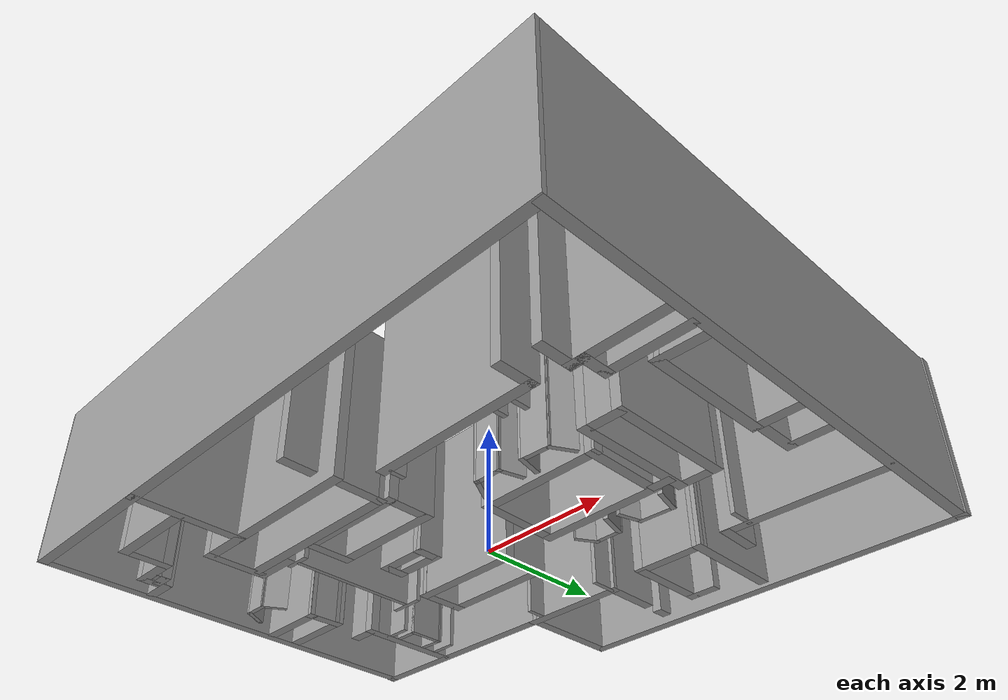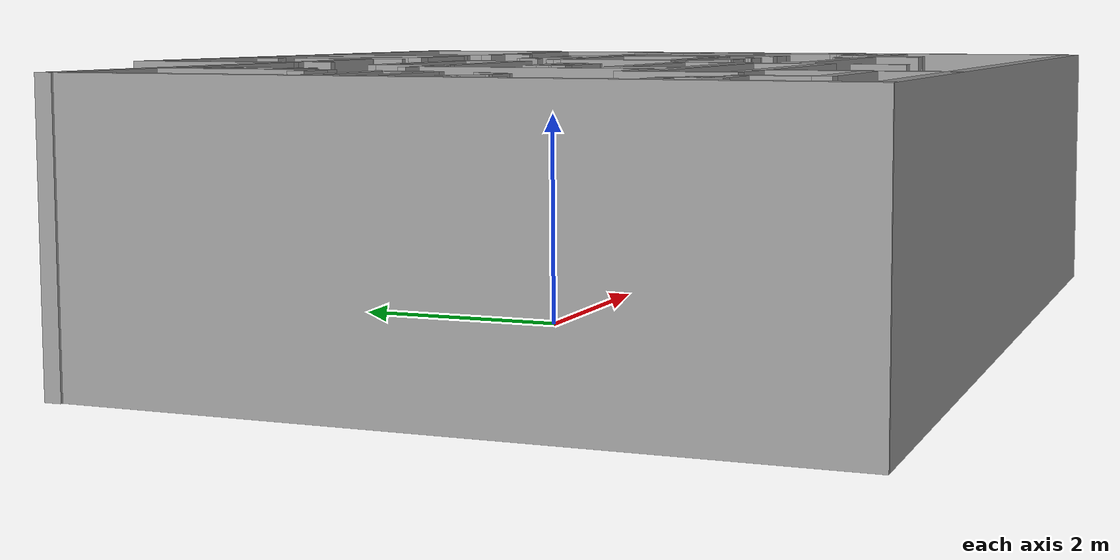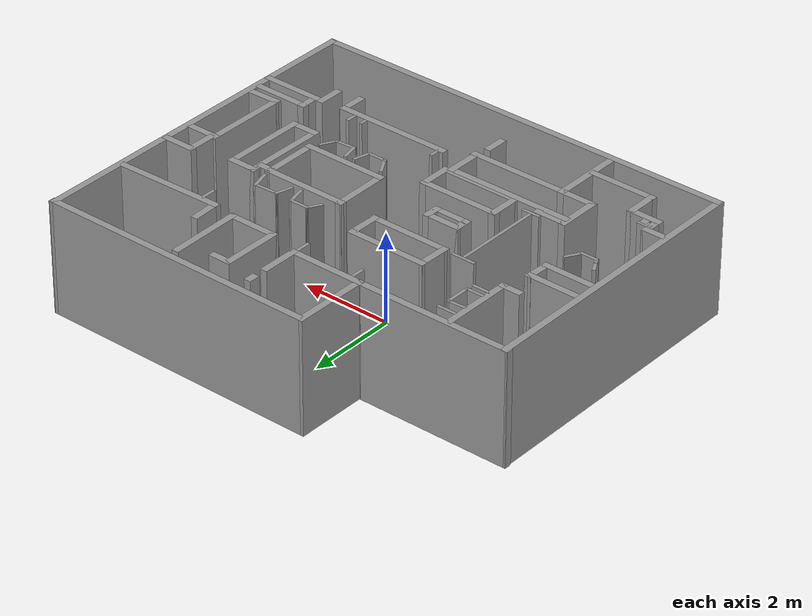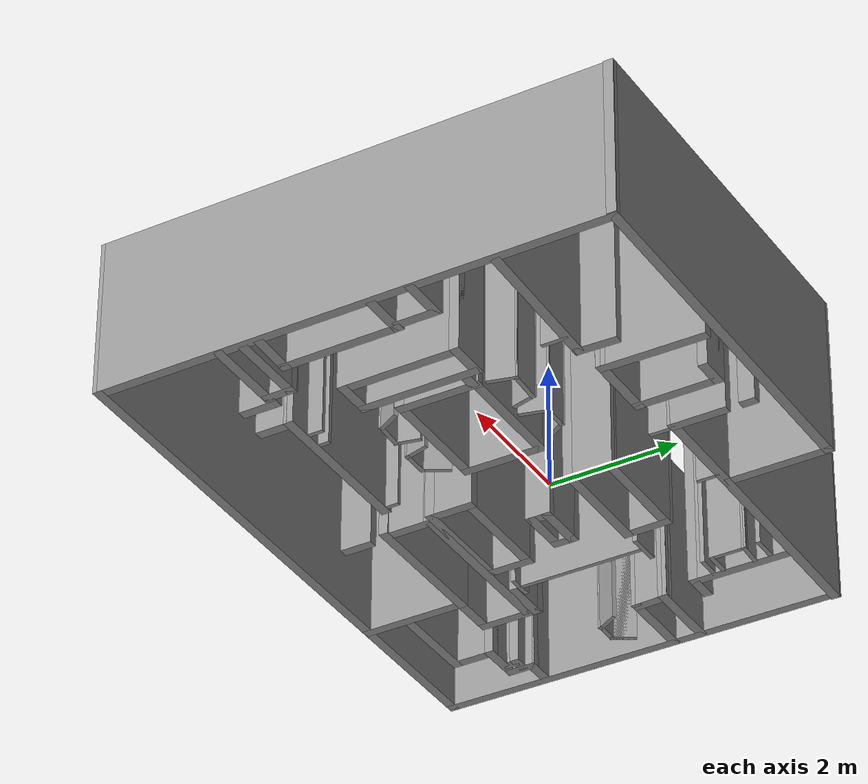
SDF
<?xml version='1.0'?>
<sdf version='1.6'>
  <model name='room4'>
    <pose frame=''>0.183294 -0.251584 0 0 -0 0</pose>
    <link name='Wall_0'>
      <collision name='Wall_0_Collision'>
        <geometry>
          <box>
            <size>8.014 0.15 2.5</size>
          </box>
        </geometry>
        <pose frame=''>0 0 1.25 0 -0 0</pose>
      </collision>
      <visual name='Wall_0_Visual'>
        <pose frame=''>0 0 1.25 0 -0 0</pose>
        <geometry>
          <box>
            <size>8.014 0.15 2.5</size>
          </box>
        </geometry>
        <material>
          <script>
            <uri>file://media/materials/scripts/gazebo.material</uri>
            <name>Gazebo/Grey</name>
          </script>
          <ambient>1 1 1 1</ambient>
        </material>
        <meta>
          <layer>0</layer>
        </meta>
      </visual>
      <pose frame=''>4.74429 0.03461 0 0 -0 -1.56965</pose>
    </link>
    <link name='Wall_1'>
      <collision name='Wall_1_Collision'>
        <geometry>
          <box>
            <size>9.58911 0.15 2.5</size>
          </box>
        </geometry>
        <pose frame=''>0 0 1.25 0 -0 0</pose>
      </collision>
      <visual name='Wall_1_Visual'>
        <pose frame=''>0 0 1.25 0 -0 0</pose>
        <geometry>
          <box>
            <size>9.58911 0.15 2.5</size>
          </box>
        </geometry>
        <material>
          <script>
            <uri>file://media/materials/scripts/gazebo.material</uri>
            <name>Gazebo/Grey</name>
          </script>
          <ambient>1 1 1 1</ambient>
        </material>
        <meta>
          <layer>0</layer>
        </meta>
      </visual>
      <pose frame=''>0.029286 -3.94339 0 0 -0 -3.13672</pose>
    </link>
    <link name='Wall_10'>
      <collision name='Wall_10_Collision'>
        <geometry>
          <box>
            <size>1.65013 0.15 2.5</size>
          </box>
        </geometry>
        <pose frame=''>0 0 1.25 0 -0 0</pose>
      </collision>
      <visual name='Wall_10_Visual'>
        <pose frame=''>0 0 1.25 0 -0 0</pose>
        <geometry>
          <box>
            <size>1.65013 0.15 2.5</size>
          </box>
        </geometry>
        <material>
          <script>
            <uri>file://media/materials/scripts/gazebo.material</uri>
            <name>Gazebo/Grey</name>
          </script>
          <ambient>1 1 1 1</ambient>
        </material>
        <meta>
          <layer>0</layer>
        </meta>
      </visual>
      <pose frame=''>1.86988 2.9697 0 0 -0 -1.55746</pose>
    </link>
    <link name='Wall_101'>
      <collision name='Wall_101_Collision'>
        <geometry>
          <box>
            <size>0.5 0.15 2.5</size>
          </box>
        </geometry>
        <pose frame=''>0 0 1.25 0 -0 0</pose>
      </collision>
      <visual name='Wall_101_Visual'>
        <pose frame=''>0 0 1.25 0 -0 0</pose>
        <geometry>
          <box>
            <size>0.5 0.15 2.5</size>
          </box>
        </geometry>
        <material>
          <script>
            <uri>file://media/materials/scripts/gazebo.material</uri>
            <name>Gazebo/Grey</name>
          </script>
          <ambient>1 1 1 1</ambient>
        </material>
        <meta>
          <layer>0</layer>
        </meta>
      </visual>
      <pose frame=''>-0.238275 -2.90211 0 0 -0 1.5708</pose>
    </link>
    <link name='Wall_103'>
      <collision name='Wall_103_Collision'>
        <geometry>
          <box>
            <size>0.85 0.15 2.5</size>
          </box>
        </geometry>
        <pose frame=''>0 0 1.25 0 -0 0</pose>
      </collision>
      <visual name='Wall_103_Visual'>
        <pose frame=''>0 0 1.25 0 -0 0</pose>
        <geometry>
          <box>
            <size>0.85 0.15 2.5</size>
          </box>
        </geometry>
        <material>
          <script>
            <uri>file://media/materials/scripts/gazebo.material</uri>
            <name>Gazebo/Grey</name>
          </script>
          <ambient>1 1 1 1</ambient>
        </material>
        <meta>
          <layer>0</layer>
        </meta>
      </visual>
      <pose frame=''>-1.20078 -0.157139 0 0 -0 0</pose>
    </link>
    <link name='Wall_105'>
      <collision name='Wall_105_Collision'>
        <geometry>
          <box>
            <size>0.4 0.15 2.5</size>
          </box>
        </geometry>
        <pose frame=''>0 0 1.25 0 -0 0</pose>
      </collision>
      <visual name='Wall_105_Visual'>
        <pose frame=''>0 0 1.25 0 -0 0</pose>
        <geometry>
          <box>
            <size>0.4 0.15 2.5</size>
          </box>
        </geometry>
        <material>
          <script>
            <uri>file://media/materials/scripts/gazebo.material</uri>
            <name>Gazebo/Grey</name>
          </script>
          <ambient>1 1 1 1</ambient>
        </material>
        <meta>
          <layer>0</layer>
        </meta>
      </visual>
      <pose frame=''>-0.850776 -0.282139 0 0 -0 -1.5708</pose>
    </link>
    <link name='Wall_109'>
      <collision name='Wall_109_Collision'>
        <geometry>
          <box>
            <size>0.4 0.15 2.5</size>
          </box>
        </geometry>
        <pose frame=''>0 0 1.25 0 -0 0</pose>
      </collision>
      <visual name='Wall_109_Visual'>
        <pose frame=''>0 0 1.25 0 -0 0</pose>
        <geometry>
          <box>
            <size>0.4 0.15 2.5</size>
          </box>
        </geometry>
        <material>
          <script>
            <uri>file://media/materials/scripts/gazebo.material</uri>
            <name>Gazebo/Grey</name>
          </script>
          <ambient>1 1 1 1</ambient>
        </material>
        <meta>
          <layer>0</layer>
        </meta>
      </visual>
      <pose frame=''>-1.55078 -0.282139 0 0 -0 -1.5708</pose>
    </link>
    <link name='Wall_11'>
      <collision name='Wall_11_Collision'>
        <geometry>
          <box>
            <size>1.15 0.15 2.5</size>
          </box>
        </geometry>
        <pose frame=''>0 0 1.25 0 -0 0</pose>
      </collision>
      <visual name='Wall_11_Visual'>
        <pose frame=''>0 0 1.25 0 -0 0</pose>
        <geometry>
          <box>
            <size>1.15 0.15 2.5</size>
          </box>
        </geometry>
        <material>
          <script>
            <uri>file://media/materials/scripts/gazebo.material</uri>
            <name>Gazebo/Grey</name>
          </script>
          <ambient>1 1 1 1</ambient>
        </material>
        <meta>
          <layer>0</layer>
        </meta>
      </visual>
      <pose frame=''>1.37988 2.2197 0 0 -0 3.14159</pose>
    </link>
    <link name='Wall_116'>
      <collision name='Wall_116_Collision'>
        <geometry>
          <box>
            <size>0.85 0.15 2.5</size>
          </box>
        </geometry>
        <pose frame=''>0 0 1.25 0 -0 0</pose>
      </collision>
      <visual name='Wall_116_Visual'>
        <pose frame=''>0 0 1.25 0 -0 0</pose>
        <geometry>
          <box>
            <size>0.85 0.15 2.5</size>
          </box>
        </geometry>
        <material>
          <script>
            <uri>file://media/materials/scripts/gazebo.material</uri>
            <name>Gazebo/Grey</name>
          </script>
          <ambient>1 1 1 1</ambient>
        </material>
        <meta>
          <layer>0</layer>
        </meta>
      </visual>
      <pose frame=''>-1.20078 -0.407139 0 0 -0 0</pose>
    </link>
    <link name='Wall_118'>
      <collision name='Wall_118_Collision'>
        <geometry>
          <box>
            <size>0.35 0.07 2.5</size>
          </box>
        </geometry>
        <pose frame=''>0 0 1.25 0 -0 0</pose>
      </collision>
      <visual name='Wall_118_Visual'>
        <pose frame=''>0 0 1.25 0 -0 0</pose>
        <geometry>
          <box>
            <size>0.35 0.07 2.5</size>
          </box>
        </geometry>
        <material>
          <script>
            <uri>file://media/materials/scripts/gazebo.material</uri>
            <name>Gazebo/Grey</name>
          </script>
          <ambient>1 1 1 1</ambient>
        </material>
        <meta>
          <layer>0</layer>
        </meta>
      </visual>
      <pose frame=''>-1.15474 2.22246 0 0 -0 1.5708</pose>
    </link>
    <link name='Wall_126'>
      <collision name='Wall_126_Collision'>
        <geometry>
          <box>
            <size>0.43 0.07 2.5</size>
          </box>
        </geometry>
        <pose frame=''>0 0 1.25 0 -0 0</pose>
      </collision>
      <visual name='Wall_126_Visual'>
        <pose frame=''>0 0 1.25 0 -0 0</pose>
        <geometry>
          <box>
            <size>0.43 0.07 2.5</size>
          </box>
        </geometry>
        <material>
          <script>
            <uri>file://media/materials/scripts/gazebo.material</uri>
            <name>Gazebo/Grey</name>
          </script>
          <ambient>1 1 1 1</ambient>
        </material>
        <meta>
          <layer>0</layer>
        </meta>
      </visual>
      <pose frame=''>0.176827 2.23103 0 0 -0 -1.5708</pose>
    </link>
    <link name='Wall_128'>
      <collision name='Wall_128_Collision'>
        <geometry>
          <box>
            <size>0.4 0.07 2.5</size>
          </box>
        </geometry>
        <pose frame=''>0 0 1.25 0 -0 0</pose>
      </collision>
      <visual name='Wall_128_Visual'>
        <pose frame=''>0 0 1.25 0 -0 0</pose>
        <geometry>
          <box>
            <size>0.4 0.07 2.5</size>
          </box>
        </geometry>
        <material>
          <script>
            <uri>file://media/materials/scripts/gazebo.material</uri>
            <name>Gazebo/Grey</name>
          </script>
          <ambient>1 1 1 1</ambient>
        </material>
        <meta>
          <layer>0</layer>
        </meta>
      </visual>
      <pose frame=''>2.73621 1.96934 0 0 -0 -1.5708</pose>
    </link>
    <link name='Wall_13'>
      <collision name='Wall_13_Collision'>
        <geometry>
          <box>
            <size>1.35 0.15 2.5</size>
          </box>
        </geometry>
        <pose frame=''>0 0 1.25 0 -0 0</pose>
      </collision>
      <visual name='Wall_13_Visual'>
        <pose frame=''>0 0 1.25 0 -0 0</pose>
        <geometry>
          <box>
            <size>1.35 0.15 2.5</size>
          </box>
        </geometry>
        <material>
          <script>
            <uri>file://media/materials/scripts/gazebo.material</uri>
            <name>Gazebo/Grey</name>
          </script>
          <ambient>1 1 1 1</ambient>
        </material>
        <meta>
          <layer>0</layer>
        </meta>
      </visual>
      <pose frame=''>0.87988 2.8197 0 0 -0 1.5708</pose>
    </link>
    <link name='Wall_130'>
      <collision name='Wall_130_Collision'>
        <geometry>
          <box>
            <size>2.6 0.15 2.5</size>
          </box>
        </geometry>
        <pose frame=''>0 0 1.25 0 -0 0</pose>
      </collision>
      <visual name='Wall_130_Visual'>
        <pose frame=''>0 0 1.25 0 -0 0</pose>
        <geometry>
          <box>
            <size>2.6 0.15 2.5</size>
          </box>
        </geometry>
        <material>
          <script>
            <uri>file://media/materials/scripts/gazebo.material</uri>
            <name>Gazebo/Grey</name>
          </script>
          <ambient>1 1 1 1</ambient>
        </material>
        <meta>
          <layer>0</layer>
        </meta>
      </visual>
      <pose frame=''>1.62664 -2.08518 0 0 -0 0</pose>
    </link>
    <link name='Wall_132'>
      <collision name='Wall_132_Collision'>
        <geometry>
          <box>
            <size>0.25 0.07 2.5</size>
          </box>
        </geometry>
        <pose frame=''>0 0 1.25 0 -0 0</pose>
      </collision>
      <visual name='Wall_132_Visual'>
        <pose frame=''>0 0 1.25 0 -0 0</pose>
        <geometry>
          <box>
            <size>0.25 0.07 2.5</size>
          </box>
        </geometry>
        <material>
          <script>
            <uri>file://media/materials/scripts/gazebo.material</uri>
            <name>Gazebo/Grey</name>
          </script>
          <ambient>1 1 1 1</ambient>
        </material>
        <meta>
          <layer>0</layer>
        </meta>
      </visual>
      <pose frame=''>0.453516 -1.93307 0 0 -0 -1.5708</pose>
    </link>
    <link name='Wall_134'>
      <collision name='Wall_134_Collision'>
        <geometry>
          <box>
            <size>0.170242 0.07 2.5</size>
          </box>
        </geometry>
        <pose frame=''>0 0 1.25 0 -0 0</pose>
      </collision>
      <visual name='Wall_134_Visual'>
        <pose frame=''>0 0 1.25 0 -0 0</pose>
        <geometry>
          <box>
            <size>0.170242 0.07 2.5</size>
          </box>
        </geometry>
        <material>
          <script>
            <uri>file://media/materials/scripts/gazebo.material</uri>
            <name>Gazebo/Grey</name>
          </script>
          <ambient>1 1 1 1</ambient>
        </material>
        <meta>
          <layer>0</layer>
        </meta>
      </visual>
      <pose frame=''>2.23471 -1.92742 0 0 -0 -1.5708</pose>
    </link>
    <link name='Wall_136'>
      <collision name='Wall_136_Collision'>
        <geometry>
          <box>
            <size>0.3 0.07 2.5</size>
          </box>
        </geometry>
        <pose frame=''>0 0 1.25 0 -0 0</pose>
      </collision>
      <visual name='Wall_136_Visual'>
        <pose frame=''>0 0 1.25 0 -0 0</pose>
        <geometry>
          <box>
            <size>0.3 0.07 2.5</size>
          </box>
        </geometry>
        <material>
          <script>
            <uri>file://media/materials/scripts/gazebo.material</uri>
            <name>Gazebo/Grey</name>
          </script>
          <ambient>1 1 1 1</ambient>
        </material>
        <meta>
          <layer>0</layer>
        </meta>
      </visual>
      <pose frame=''>2.51095 -1.92354 0 0 -0 -1.5708</pose>
    </link>
    <link name='Wall_138'>
      <collision name='Wall_138_Collision'>
        <geometry>
          <box>
            <size>0.6 0.15 2.5</size>
          </box>
        </geometry>
        <pose frame=''>0 0 1.25 0 -0 0</pose>
      </collision>
      <visual name='Wall_138_Visual'>
        <pose frame=''>0 0 1.25 0 -0 0</pose>
        <geometry>
          <box>
            <size>0.6 0.15 2.5</size>
          </box>
        </geometry>
        <material>
          <script>
            <uri>file://media/materials/scripts/gazebo.material</uri>
            <name>Gazebo/Grey</name>
          </script>
          <ambient>1 1 1 1</ambient>
        </material>
        <meta>
          <layer>0</layer>
        </meta>
      </visual>
      <pose frame=''>2.85164 -2.31018 0 0 -0 -1.5708</pose>
    </link>
    <link name='Wall_140'>
      <collision name='Wall_140_Collision'>
        <geometry>
          <box>
            <size>1.5 0.15 2.5</size>
          </box>
        </geometry>
        <pose frame=''>0 0 1.25 0 -0 0</pose>
      </collision>
      <visual name='Wall_140_Visual'>
        <pose frame=''>0 0 1.25 0 -0 0</pose>
        <geometry>
          <box>
            <size>1.5 0.15 2.5</size>
          </box>
        </geometry>
        <material>
          <script>
            <uri>file://media/materials/scripts/gazebo.material</uri>
            <name>Gazebo/Grey</name>
          </script>
          <ambient>1 1 1 1</ambient>
        </material>
        <meta>
          <layer>0</layer>
        </meta>
      </visual>
      <pose frame=''>4.04991 -2.016 0 0 -0 3.14159</pose>
    </link>
    <link name='Wall_141'>
      <collision name='Wall_141_Collision'>
        <geometry>
          <box>
            <size>0.6 0.15 2.5</size>
          </box>
        </geometry>
        <pose frame=''>0 0 1.25 0 -0 0</pose>
      </collision>
      <visual name='Wall_141_Visual'>
        <pose frame=''>0 0 1.25 0 -0 0</pose>
        <geometry>
          <box>
            <size>0.6 0.15 2.5</size>
          </box>
        </geometry>
        <material>
          <script>
            <uri>file://media/materials/scripts/gazebo.material</uri>
            <name>Gazebo/Grey</name>
          </script>
          <ambient>1 1 1 1</ambient>
        </material>
        <meta>
          <layer>0</layer>
        </meta>
      </visual>
      <pose frame=''>3.37491 -2.241 0 0 -0 -1.5708</pose>
    </link>
    <link name='Wall_143'>
      <collision name='Wall_143_Collision'>
        <geometry>
          <box>
            <size>0.756466 0.15 2.5</size>
          </box>
        </geometry>
        <pose frame=''>0 0 1.25 0 -0 0</pose>
      </collision>
      <visual name='Wall_143_Visual'>
        <pose frame=''>0 0 1.25 0 -0 0</pose>
        <geometry>
          <box>
            <size>0.756466 0.15 2.5</size>
          </box>
        </geometry>
        <material>
          <script>
            <uri>file://media/materials/scripts/gazebo.material</uri>
            <name>Gazebo/Grey</name>
          </script>
          <ambient>1 1 1 1</ambient>
        </material>
        <meta>
          <layer>0</layer>
        </meta>
      </visual>
      <pose frame=''>4.35251 -1.41939 0 0 -0 -3.11309</pose>
    </link>
    <link name='Wall_145'>
      <collision name='Wall_145_Collision'>
        <geometry>
          <box>
            <size>1.9 0.15 2.5</size>
          </box>
        </geometry>
        <pose frame=''>0 0 1.25 0 -0 0</pose>
      </collision>
      <visual name='Wall_145_Visual'>
        <pose frame=''>0 0 1.25 0 -0 0</pose>
        <geometry>
          <box>
            <size>1.9 0.15 2.5</size>
          </box>
        </geometry>
        <material>
          <script>
            <uri>file://media/materials/scripts/gazebo.material</uri>
            <name>Gazebo/Grey</name>
          </script>
          <ambient>1 1 1 1</ambient>
        </material>
        <meta>
          <layer>0</layer>
        </meta>
      </visual>
      <pose frame=''>4.04927 -0.553037 0 0 -0 1.5708</pose>
    </link>
    <link name='Wall_147'>
      <collision name='Wall_147_Collision'>
        <geometry>
          <box>
            <size>0.67 0.15 2.5</size>
          </box>
        </geometry>
        <pose frame=''>0 0 1.25 0 -0 0</pose>
      </collision>
      <visual name='Wall_147_Visual'>
        <pose frame=''>0 0 1.25 0 -0 0</pose>
        <geometry>
          <box>
            <size>0.67 0.15 2.5</size>
          </box>
        </geometry>
        <material>
          <script>
            <uri>file://media/materials/scripts/gazebo.material</uri>
            <name>Gazebo/Grey</name>
          </script>
          <ambient>1 1 1 1</ambient>
        </material>
        <meta>
          <layer>0</layer>
        </meta>
      </visual>
      <pose frame=''>2.94433 -1.013 0 0 -0 0</pose>
    </link>
    <link name='Wall_149'>
      <collision name='Wall_149_Collision'>
        <geometry>
          <box>
            <size>1.9 0.15 2.5</size>
          </box>
        </geometry>
        <pose frame=''>0 0 1.25 0 -0 0</pose>
      </collision>
      <visual name='Wall_149_Visual'>
        <pose frame=''>0 0 1.25 0 -0 0</pose>
        <geometry>
          <box>
            <size>1.9 0.15 2.5</size>
          </box>
        </geometry>
        <material>
          <script>
            <uri>file://media/materials/scripts/gazebo.material</uri>
            <name>Gazebo/Grey</name>
          </script>
          <ambient>1 1 1 1</ambient>
        </material>
        <meta>
          <layer>0</layer>
        </meta>
      </visual>
      <pose frame=''>3.20433 -0.138003 0 0 -0 1.5708</pose>
    </link>
    <link name='Wall_15'>
      <collision name='Wall_15_Collision'>
        <geometry>
          <box>
            <size>0.9 0.15 2.5</size>
          </box>
        </geometry>
        <pose frame=''>0 0 1.25 0 -0 0</pose>
      </collision>
      <visual name='Wall_15_Visual'>
        <pose frame=''>0 0 1.25 0 -0 0</pose>
        <geometry>
          <box>
            <size>0.9 0.15 2.5</size>
          </box>
        </geometry>
        <material>
          <script>
            <uri>file://media/materials/scripts/gazebo.material</uri>
            <name>Gazebo/Grey</name>
          </script>
          <ambient>1 1 1 1</ambient>
        </material>
        <meta>
          <layer>0</layer>
        </meta>
      </visual>
      <pose frame=''>0.19988 2.7847 0 0 -0 -1.5708</pose>
    </link>
    <link name='Wall_151'>
      <collision name='Wall_151_Collision'>
        <geometry>
          <box>
            <size>0.75 0.15 2.5</size>
          </box>
        </geometry>
        <pose frame=''>0 0 1.25 0 -0 0</pose>
      </collision>
      <visual name='Wall_151_Visual'>
        <pose frame=''>0 0 1.25 0 -0 0</pose>
        <geometry>
          <box>
            <size>0.75 0.15 2.5</size>
          </box>
        </geometry>
        <material>
          <script>
            <uri>file://media/materials/scripts/gazebo.material</uri>
            <name>Gazebo/Grey</name>
          </script>
          <ambient>1 1 1 1</ambient>
        </material>
        <meta>
          <layer>0</layer>
        </meta>
      </visual>
      <pose frame=''>4.34927 0.321963 0 0 -0 0</pose>
    </link>
    <link name='Wall_153'>
      <collision name='Wall_153_Collision'>
        <geometry>
          <box>
            <size>0.75 0.15 2.5</size>
          </box>
        </geometry>
        <pose frame=''>0 0 1.25 0 -0 0</pose>
      </collision>
      <visual name='Wall_153_Visual'>
        <pose frame=''>0 0 1.25 0 -0 0</pose>
        <geometry>
          <box>
            <size>0.75 0.15 2.5</size>
          </box>
        </geometry>
        <material>
          <script>
            <uri>file://media/materials/scripts/gazebo.material</uri>
            <name>Gazebo/Grey</name>
          </script>
          <ambient>1 1 1 1</ambient>
        </material>
        <meta>
          <layer>0</layer>
        </meta>
      </visual>
      <pose frame=''>4.40762 0.941118 0 0 -0 3.14159</pose>
    </link>
    <link name='Wall_154'>
      <collision name='Wall_154_Collision'>
        <geometry>
          <box>
            <size>0.7 0.15 2.5</size>
          </box>
        </geometry>
        <pose frame=''>0 0 1.25 0 -0 0</pose>
      </collision>
      <visual name='Wall_154_Visual'>
        <pose frame=''>0 0 1.25 0 -0 0</pose>
        <geometry>
          <box>
            <size>0.7 0.15 2.5</size>
          </box>
        </geometry>
        <material>
          <script>
            <uri>file://media/materials/scripts/gazebo.material</uri>
            <name>Gazebo/Grey</name>
          </script>
          <ambient>1 1 1 1</ambient>
        </material>
        <meta>
          <layer>0</layer>
        </meta>
      </visual>
      <pose frame=''>4.10762 0.666118 0 0 -0 -1.5708</pose>
    </link>
    <link name='Wall_156'>
      <collision name='Wall_156_Collision'>
        <geometry>
          <box>
            <size>0.67 0.15 2.5</size>
          </box>
        </geometry>
        <pose frame=''>0 0 1.25 0 -0 0</pose>
      </collision>
      <visual name='Wall_156_Visual'>
        <pose frame=''>0 0 1.25 0 -0 0</pose>
        <geometry>
          <box>
            <size>0.67 0.15 2.5</size>
          </box>
        </geometry>
        <material>
          <script>
            <uri>file://media/materials/scripts/gazebo.material</uri>
            <name>Gazebo/Grey</name>
          </script>
          <ambient>1 1 1 1</ambient>
        </material>
        <meta>
          <layer>0</layer>
        </meta>
      </visual>
      <pose frame=''>2.94433 0.736997 0 0 -0 3.14159</pose>
    </link>
    <link name='Wall_159'>
      <collision name='Wall_159_Collision'>
        <geometry>
          <box>
            <size>1.9 0.15 2.5</size>
          </box>
        </geometry>
        <pose frame=''>0 0 1.25 0 -0 0</pose>
      </collision>
      <visual name='Wall_159_Visual'>
        <pose frame=''>0 0 1.25 0 -0 0</pose>
        <geometry>
          <box>
            <size>1.9 0.15 2.5</size>
          </box>
        </geometry>
        <material>
          <script>
            <uri>file://media/materials/scripts/gazebo.material</uri>
            <name>Gazebo/Grey</name>
          </script>
          <ambient>1 1 1 1</ambient>
        </material>
        <meta>
          <layer>0</layer>
        </meta>
      </visual>
      <pose frame=''>2.68433 -0.138003 0 0 -0 -1.5708</pose>
    </link>
    <link name='Wall_16'>
      <collision name='Wall_16_Collision'>
        <geometry>
          <box>
            <size>1.73309 0.15 2.5</size>
          </box>
        </geometry>
        <pose frame=''>0 0 1.25 0 -0 0</pose>
      </collision>
      <visual name='Wall_16_Visual'>
        <pose frame=''>0 0 1.25 0 -0 0</pose>
        <geometry>
          <box>
            <size>1.73309 0.15 2.5</size>
          </box>
        </geometry>
        <material>
          <script>
            <uri>file://media/materials/scripts/gazebo.material</uri>
            <name>Gazebo/Grey</name>
          </script>
          <ambient>1 1 1 1</ambient>
        </material>
        <meta>
          <layer>0</layer>
        </meta>
      </visual>
      <pose frame=''>-0.591667 2.40966 0 0 -0 -3.14153</pose>
    </link>
    <link name='Wall_18'>
      <collision name='Wall_18_Collision'>
        <geometry>
          <box>
            <size>0.25 0.15 2.5</size>
          </box>
        </geometry>
        <pose frame=''>0 0 1.25 0 -0 0</pose>
      </collision>
      <visual name='Wall_18_Visual'>
        <pose frame=''>0 0 1.25 0 -0 0</pose>
        <geometry>
          <box>
            <size>0.25 0.15 2.5</size>
          </box>
        </geometry>
        <material>
          <script>
            <uri>file://media/materials/scripts/gazebo.material</uri>
            <name>Gazebo/Grey</name>
          </script>
          <ambient>1 1 1 1</ambient>
        </material>
        <meta>
          <layer>0</layer>
        </meta>
      </visual>
      <pose frame=''>0.19988 3.5497 0 0 -0 -1.5708</pose>
    </link>
    <link name='Wall_2'>
      <collision name='Wall_2_Collision'>
        <geometry>
          <box>
            <size>6.50004 0.15 2.5</size>
          </box>
        </geometry>
        <pose frame=''>0 0 1.25 0 -0 0</pose>
      </collision>
      <visual name='Wall_2_Visual'>
        <pose frame=''>0 0 1.25 0 -0 0</pose>
        <geometry>
          <box>
            <size>6.50004 0.15 2.5</size>
          </box>
        </geometry>
        <material>
          <script>
            <uri>file://media/materials/scripts/gazebo.material</uri>
            <name>Gazebo/Grey</name>
          </script>
          <ambient>1 1 1 1</ambient>
        </material>
        <meta>
          <layer>0</layer>
        </meta>
      </visual>
      <pose frame=''>-4.72471 -0.79139 0 0 -0 1.57442</pose>
    </link>
    <link name='Wall_20'>
      <collision name='Wall_20_Collision'>
        <geometry>
          <box>
            <size>0.5 0.15 2.5</size>
          </box>
        </geometry>
        <pose frame=''>0 0 1.25 0 -0 0</pose>
      </collision>
      <visual name='Wall_20_Visual'>
        <pose frame=''>0 0 1.25 0 -0 0</pose>
        <geometry>
          <box>
            <size>0.5 0.15 2.5</size>
          </box>
        </geometry>
        <material>
          <script>
            <uri>file://media/materials/scripts/gazebo.material</uri>
            <name>Gazebo/Grey</name>
          </script>
          <ambient>1 1 1 1</ambient>
        </material>
        <meta>
          <layer>0</layer>
        </meta>
      </visual>
      <pose frame=''>1.05488 3.4197 0 0 -0 0</pose>
    </link>
    <link name='Wall_22'>
      <collision name='Wall_22_Collision'>
        <geometry>
          <box>
            <size>1.65 0.15 2.5</size>
          </box>
        </geometry>
        <pose frame=''>0 0 1.25 0 -0 0</pose>
      </collision>
      <visual name='Wall_22_Visual'>
        <pose frame=''>0 0 1.25 0 -0 0</pose>
        <geometry>
          <box>
            <size>1.65 0.15 2.5</size>
          </box>
        </geometry>
        <material>
          <script>
            <uri>file://media/materials/scripts/gazebo.material</uri>
            <name>Gazebo/Grey</name>
          </script>
          <ambient>1 1 1 1</ambient>
        </material>
        <meta>
          <layer>0</layer>
        </meta>
      </visual>
      <pose frame=''>-3.42012 1.5697 0 0 -0 -1.5708</pose>
    </link>
    <link name='Wall_23'>
      <collision name='Wall_23_Collision'>
        <geometry>
          <box>
            <size>0.5 0.15 2.5</size>
          </box>
        </geometry>
        <pose frame=''>0 0 1.25 0 -0 0</pose>
      </collision>
      <visual name='Wall_23_Visual'>
        <pose frame=''>0 0 1.25 0 -0 0</pose>
        <geometry>
          <box>
            <size>0.5 0.15 2.5</size>
          </box>
        </geometry>
        <material>
          <script>
            <uri>file://media/materials/scripts/gazebo.material</uri>
            <name>Gazebo/Grey</name>
          </script>
          <ambient>1 1 1 1</ambient>
        </material>
        <meta>
          <layer>0</layer>
        </meta>
      </visual>
      <pose frame=''>-3.59512 0.819703 0 0 -0 3.14159</pose>
    </link>
    <link name='Wall_25'>
      <collision name='Wall_25_Collision'>
        <geometry>
          <box>
            <size>0.420174 0.07 2.5</size>
          </box>
        </geometry>
        <pose frame=''>0 0 1.25 0 -0 0</pose>
      </collision>
      <visual name='Wall_25_Visual'>
        <pose frame=''>0 0 1.25 0 -0 0</pose>
        <geometry>
          <box>
            <size>0.420174 0.07 2.5</size>
          </box>
        </geometry>
        <material>
          <script>
            <uri>file://media/materials/scripts/gazebo.material</uri>
            <name>Gazebo/Grey</name>
          </script>
          <ambient>1 1 1 1</ambient>
        </material>
        <meta>
          <layer>0</layer>
        </meta>
      </visual>
      <pose frame=''>-3.20529 1.15958 0 0 -0 0</pose>
    </link>
    <link name='Wall_252'>
      <collision name='Wall_252_Collision'>
        <geometry>
          <box>
            <size>0.5 0.15 2.5</size>
          </box>
        </geometry>
        <pose frame=''>0 0 1.25 0 -0 0</pose>
      </collision>
      <visual name='Wall_252_Visual'>
        <pose frame=''>0 0 1.25 0 -0 0</pose>
        <geometry>
          <box>
            <size>0.5 0.15 2.5</size>
          </box>
        </geometry>
        <material>
          <script>
            <uri>file://media/materials/scripts/gazebo.material</uri>
            <name>Gazebo/Grey</name>
          </script>
          <ambient>1 1 1 1</ambient>
        </material>
        <meta>
          <layer>0</layer>
        </meta>
      </visual>
      <pose frame=''>3.54609 -1.83378 0 0 -0 -1.5708</pose>
    </link>
    <link name='Wall_254'>
      <collision name='Wall_254_Collision'>
        <geometry>
          <box>
            <size>1.25 0.15 2.5</size>
          </box>
        </geometry>
        <pose frame=''>0 0 1.25 0 -0 0</pose>
      </collision>
      <visual name='Wall_254_Visual'>
        <pose frame=''>0 0 1.25 0 -0 0</pose>
        <geometry>
          <box>
            <size>1.25 0.15 2.5</size>
          </box>
        </geometry>
        <material>
          <script>
            <uri>file://media/materials/scripts/gazebo.material</uri>
            <name>Gazebo/Grey</name>
          </script>
          <ambient>1 1 1 1</ambient>
        </material>
        <meta>
          <layer>0</layer>
        </meta>
      </visual>
      <pose frame=''>4.09609 -1.65878 0 0 -0 0</pose>
    </link>
    <link name='Wall_256'>
      <collision name='Wall_256_Collision'>
        <geometry>
          <box>
            <size>1.30339 0.15 2.5</size>
          </box>
        </geometry>
        <pose frame=''>0 0 1.25 0 -0 0</pose>
      </collision>
      <visual name='Wall_256_Visual'>
        <pose frame=''>0 0 1.25 0 -0 0</pose>
        <geometry>
          <box>
            <size>1.30339 0.15 2.5</size>
          </box>
        </geometry>
        <material>
          <script>
            <uri>file://media/materials/scripts/gazebo.material</uri>
            <name>Gazebo/Grey</name>
          </script>
          <ambient>1 1 1 1</ambient>
        </material>
        <meta>
          <layer>0</layer>
        </meta>
      </visual>
      <pose frame=''>0.662227 -0.002843 0 0 -0 -1.55879</pose>
    </link>
    <link name='Wall_257'>
      <collision name='Wall_257_Collision'>
        <geometry>
          <box>
            <size>1.9 0.15 2.5</size>
          </box>
        </geometry>
        <pose frame=''>0 0 1.25 0 -0 0</pose>
      </collision>
      <visual name='Wall_257_Visual'>
        <pose frame=''>0 0 1.25 0 -0 0</pose>
        <geometry>
          <box>
            <size>1.9 0.15 2.5</size>
          </box>
        </geometry>
        <material>
          <script>
            <uri>file://media/materials/scripts/gazebo.material</uri>
            <name>Gazebo/Grey</name>
          </script>
          <ambient>1 1 1 1</ambient>
        </material>
        <meta>
          <layer>0</layer>
        </meta>
      </visual>
      <pose frame=''>1.55106 -0.57903 0 0 -0 0</pose>
    </link>
    <link name='Wall_259'>
      <collision name='Wall_259_Collision'>
        <geometry>
          <box>
            <size>1.9 0.15 2.5</size>
          </box>
        </geometry>
        <pose frame=''>0 0 1.25 0 -0 0</pose>
      </collision>
      <visual name='Wall_259_Visual'>
        <pose frame=''>0 0 1.25 0 -0 0</pose>
        <geometry>
          <box>
            <size>1.9 0.15 2.5</size>
          </box>
        </geometry>
        <material>
          <script>
            <uri>file://media/materials/scripts/gazebo.material</uri>
            <name>Gazebo/Grey</name>
          </script>
          <ambient>1 1 1 1</ambient>
        </material>
        <meta>
          <layer>0</layer>
        </meta>
      </visual>
      <pose frame=''>1.53031 0.573344 0 0 -0 0</pose>
    </link>
    <link name='Wall_261'>
      <collision name='Wall_261_Collision'>
        <geometry>
          <box>
            <size>1.30339 0.15 2.5</size>
          </box>
        </geometry>
        <pose frame=''>0 0 1.25 0 -0 0</pose>
      </collision>
      <visual name='Wall_261_Visual'>
        <pose frame=''>0 0 1.25 0 -0 0</pose>
        <geometry>
          <box>
            <size>1.30339 0.15 2.5</size>
          </box>
        </geometry>
        <material>
          <script>
            <uri>file://media/materials/scripts/gazebo.material</uri>
            <name>Gazebo/Grey</name>
          </script>
          <ambient>1 1 1 1</ambient>
        </material>
        <meta>
          <layer>0</layer>
        </meta>
      </visual>
      <pose frame=''>2.41223 -0.002843 0 0 -0 -1.55879</pose>
    </link>
    <link name='Wall_265'>
      <collision name='Wall_265_Collision'>
        <geometry>
          <box>
            <size>0.35 0.15 2.5</size>
          </box>
        </geometry>
        <pose frame=''>0 0 1.25 0 -0 0</pose>
      </collision>
      <visual name='Wall_265_Visual'>
        <pose frame=''>0 0 1.25 0 -0 0</pose>
        <geometry>
          <box>
            <size>0.35 0.15 2.5</size>
          </box>
        </geometry>
        <material>
          <script>
            <uri>file://media/materials/scripts/gazebo.material</uri>
            <name>Gazebo/Grey</name>
          </script>
          <ambient>1 1 1 1</ambient>
        </material>
        <meta>
          <layer>0</layer>
        </meta>
      </visual>
      <pose frame=''>2.54833 0.536752 0 0 -0 0</pose>
    </link>
    <link name='Wall_267'>
      <collision name='Wall_267_Collision'>
        <geometry>
          <box>
            <size>0.35 0.07 2.5</size>
          </box>
        </geometry>
        <pose frame=''>0 0 1.25 0 -0 0</pose>
      </collision>
      <visual name='Wall_267_Visual'>
        <pose frame=''>0 0 1.25 0 -0 0</pose>
        <geometry>
          <box>
            <size>0.35 0.07 2.5</size>
          </box>
        </geometry>
        <material>
          <script>
            <uri>file://media/materials/scripts/gazebo.material</uri>
            <name>Gazebo/Grey</name>
          </script>
          <ambient>1 1 1 1</ambient>
        </material>
        <meta>
          <layer>0</layer>
        </meta>
      </visual>
      <pose frame=''>0.944863 0.987325 0 0 -0 1.0472</pose>
    </link>
    <link name='Wall_271'>
      <collision name='Wall_271_Collision'>
        <geometry>
          <box>
            <size>0.45 0.07 2.5</size>
          </box>
        </geometry>
        <pose frame=''>0 0 1.25 0 -0 0</pose>
      </collision>
      <visual name='Wall_271_Visual'>
        <pose frame=''>0 0 1.25 0 -0 0</pose>
        <geometry>
          <box>
            <size>0.45 0.07 2.5</size>
          </box>
        </geometry>
        <material>
          <script>
            <uri>file://media/materials/scripts/gazebo.material</uri>
            <name>Gazebo/Grey</name>
          </script>
          <ambient>1 1 1 1</ambient>
        </material>
        <meta>
          <layer>0</layer>
        </meta>
      </visual>
      <pose frame=''>1.20486 1.10857 0 0 -0 0</pose>
    </link>
    <link name='Wall_273'>
      <collision name='Wall_273_Collision'>
        <geometry>
          <box>
            <size>0.45 0.07 2.5</size>
          </box>
        </geometry>
        <pose frame=''>0 0 1.25 0 -0 0</pose>
      </collision>
      <visual name='Wall_273_Visual'>
        <pose frame=''>0 0 1.25 0 -0 0</pose>
        <geometry>
          <box>
            <size>0.45 0.07 2.5</size>
          </box>
        </geometry>
        <material>
          <script>
            <uri>file://media/materials/scripts/gazebo.material</uri>
            <name>Gazebo/Grey</name>
          </script>
          <ambient>1 1 1 1</ambient>
        </material>
        <meta>
          <layer>0</layer>
        </meta>
      </visual>
      <pose frame=''>1.44404 0.925043 0 0 -0 -1.309</pose>
    </link>
    <link name='Wall_275'>
      <collision name='Wall_275_Collision'>
        <geometry>
          <box>
            <size>0.4 0.07 2.5</size>
          </box>
        </geometry>
        <pose frame=''>0 0 1.25 0 -0 0</pose>
      </collision>
      <visual name='Wall_275_Visual'>
        <pose frame=''>0 0 1.25 0 -0 0</pose>
        <geometry>
          <box>
            <size>0.4 0.07 2.5</size>
          </box>
        </geometry>
        <material>
          <script>
            <uri>file://media/materials/scripts/gazebo.material</uri>
            <name>Gazebo/Grey</name>
          </script>
          <ambient>1 1 1 1</ambient>
        </material>
        <meta>
          <layer>0</layer>
        </meta>
      </visual>
      <pose frame=''>1.74089 0.933979 0 0 -0 1.309</pose>
    </link>
    <link name='Wall_279'>
      <collision name='Wall_279_Collision'>
        <geometry>
          <box>
            <size>0.568674 0.07 2.5</size>
          </box>
        </geometry>
        <pose frame=''>0 0 1.25 0 -0 0</pose>
      </collision>
      <visual name='Wall_279_Visual'>
        <pose frame=''>0 0 1.25 0 -0 0</pose>
        <geometry>
          <box>
            <size>0.568674 0.07 2.5</size>
          </box>
        </geometry>
        <material>
          <script>
            <uri>file://media/materials/scripts/gazebo.material</uri>
            <name>Gazebo/Grey</name>
          </script>
          <ambient>1 1 1 1</ambient>
        </material>
        <meta>
          <layer>0</layer>
        </meta>
      </visual>
      <pose frame=''>2.03278 1.10565 0 0 -0 0.049307</pose>
    </link>
    <link name='Wall_28'>
      <collision name='Wall_28_Collision'>
        <geometry>
          <box>
            <size>0.420571 0.07 2.5</size>
          </box>
        </geometry>
        <pose frame=''>0 0 1.25 0 -0 0</pose>
      </collision>
      <visual name='Wall_28_Visual'>
        <pose frame=''>0 0 1.25 0 -0 0</pose>
        <geometry>
          <box>
            <size>0.420571 0.07 2.5</size>
          </box>
        </geometry>
        <material>
          <script>
            <uri>file://media/materials/scripts/gazebo.material</uri>
            <name>Gazebo/Grey</name>
          </script>
          <ambient>1 1 1 1</ambient>
        </material>
        <meta>
          <layer>0</layer>
        </meta>
      </visual>
      <pose frame=''>-3.16529 1.82958 0 0 -0 0.057081</pose>
    </link>
    <link name='Wall_281'>
      <collision name='Wall_281_Collision'>
        <geometry>
          <box>
            <size>0.45 0.07 2.5</size>
          </box>
        </geometry>
        <pose frame=''>0 0 1.25 0 -0 0</pose>
      </collision>
      <visual name='Wall_281_Visual'>
        <pose frame=''>0 0 1.25 0 -0 0</pose>
        <geometry>
          <box>
            <size>0.45 0.07 2.5</size>
          </box>
        </geometry>
        <material>
          <script>
            <uri>file://media/materials/scripts/gazebo.material</uri>
            <name>Gazebo/Grey</name>
          </script>
          <ambient>1 1 1 1</ambient>
        </material>
        <meta>
          <layer>0</layer>
        </meta>
      </visual>
      <pose frame=''>2.33113 0.934424 0 0 -0 -1.309</pose>
    </link>
    <link name='Wall_283'>
      <collision name='Wall_283_Collision'>
        <geometry>
          <box>
            <size>0.4 0.07 2.5</size>
          </box>
        </geometry>
        <pose frame=''>0 0 1.25 0 -0 0</pose>
      </collision>
      <visual name='Wall_283_Visual'>
        <pose frame=''>0 0 1.25 0 -0 0</pose>
        <geometry>
          <box>
            <size>0.4 0.07 2.5</size>
          </box>
        </geometry>
        <material>
          <script>
            <uri>file://media/materials/scripts/gazebo.material</uri>
            <name>Gazebo/Grey</name>
          </script>
          <ambient>1 1 1 1</ambient>
        </material>
        <meta>
          <layer>0</layer>
        </meta>
      </visual>
      <pose frame=''>1.42562 -0.947992 0 0 -0 -1.8326</pose>
    </link>
    <link name='Wall_285'>
      <collision name='Wall_285_Collision'>
        <geometry>
          <box>
            <size>0.45 0.07 2.5</size>
          </box>
        </geometry>
        <pose frame=''>0 0 1.25 0 -0 0</pose>
      </collision>
      <visual name='Wall_285_Visual'>
        <pose frame=''>0 0 1.25 0 -0 0</pose>
        <geometry>
          <box>
            <size>0.45 0.07 2.5</size>
          </box>
        </geometry>
        <material>
          <script>
            <uri>file://media/materials/scripts/gazebo.material</uri>
            <name>Gazebo/Grey</name>
          </script>
          <ambient>1 1 1 1</ambient>
        </material>
        <meta>
          <layer>0</layer>
        </meta>
      </visual>
      <pose frame=''>1.19291 -1.10737 0 0 -0 3.14159</pose>
    </link>
    <link name='Wall_287'>
      <collision name='Wall_287_Collision'>
        <geometry>
          <box>
            <size>0.45 0.07 2.5</size>
          </box>
        </geometry>
        <pose frame=''>0 0 1.25 0 -0 0</pose>
      </collision>
      <visual name='Wall_287_Visual'>
        <pose frame=''>0 0 1.25 0 -0 0</pose>
        <geometry>
          <box>
            <size>0.45 0.07 2.5</size>
          </box>
        </geometry>
        <material>
          <script>
            <uri>file://media/materials/scripts/gazebo.material</uri>
            <name>Gazebo/Grey</name>
          </script>
          <ambient>1 1 1 1</ambient>
        </material>
        <meta>
          <layer>0</layer>
        </meta>
      </visual>
      <pose frame=''>0.907915 -0.942825 0 0 -0 2.0944</pose>
    </link>
    <link name='Wall_29'>
      <collision name='Wall_29_Collision'>
        <geometry>
          <box>
            <size>0.59 0.07 2.5</size>
          </box>
        </geometry>
        <pose frame=''>0 0 1.25 0 -0 0</pose>
      </collision>
      <visual name='Wall_29_Visual'>
        <pose frame=''>0 0 1.25 0 -0 0</pose>
        <geometry>
          <box>
            <size>0.59 0.07 2.5</size>
          </box>
        </geometry>
        <material>
          <script>
            <uri>file://media/materials/scripts/gazebo.material</uri>
            <name>Gazebo/Grey</name>
          </script>
          <ambient>1 1 1 1</ambient>
        </material>
        <meta>
          <layer>0</layer>
        </meta>
      </visual>
      <pose frame=''>-2.99029 1.57958 0 0 -0 -1.5708</pose>
    </link>
    <link name='Wall_290'>
      <collision name='Wall_290_Collision'>
        <geometry>
          <box>
            <size>0.392958 0.07 2.5</size>
          </box>
        </geometry>
        <pose frame=''>0 0 1.25 0 -0 0</pose>
      </collision>
      <visual name='Wall_290_Visual'>
        <pose frame=''>0 0 1.25 0 -0 0</pose>
        <geometry>
          <box>
            <size>0.392958 0.07 2.5</size>
          </box>
        </geometry>
        <material>
          <script>
            <uri>file://media/materials/scripts/gazebo.material</uri>
            <name>Gazebo/Grey</name>
          </script>
          <ambient>1 1 1 1</ambient>
        </material>
        <meta>
          <layer>0</layer>
        </meta>
      </visual>
      <pose frame=''>2.23538 -0.902968 0 0 -0 -2.06676</pose>
    </link>
    <link name='Wall_292'>
      <collision name='Wall_292_Collision'>
        <geometry>
          <box>
            <size>0.485706 0.07 2.5</size>
          </box>
        </geometry>
        <pose frame=''>0 0 1.25 0 -0 0</pose>
      </collision>
      <visual name='Wall_292_Visual'>
        <pose frame=''>0 0 1.25 0 -0 0</pose>
        <geometry>
          <box>
            <size>0.485706 0.07 2.5</size>
          </box>
        </geometry>
        <material>
          <script>
            <uri>file://media/materials/scripts/gazebo.material</uri>
            <name>Gazebo/Grey</name>
          </script>
          <ambient>1 1 1 1</ambient>
        </material>
        <meta>
          <layer>0</layer>
        </meta>
      </visual>
      <pose frame=''>1.9508 -1.06568 0 0 -0 -3.07539</pose>
    </link>
    <link name='Wall_294'>
      <collision name='Wall_294_Collision'>
        <geometry>
          <box>
            <size>0.4 0.07 2.5</size>
          </box>
        </geometry>
        <pose frame=''>0 0 1.25 0 -0 0</pose>
      </collision>
      <visual name='Wall_294_Visual'>
        <pose frame=''>0 0 1.25 0 -0 0</pose>
        <geometry>
          <box>
            <size>0.4 0.07 2.5</size>
          </box>
        </geometry>
        <material>
          <script>
            <uri>file://media/materials/scripts/gazebo.material</uri>
            <name>Gazebo/Grey</name>
          </script>
          <ambient>1 1 1 1</ambient>
        </material>
        <meta>
          <layer>0</layer>
        </meta>
      </visual>
      <pose frame=''>1.70604 -0.91866 0 0 -0 1.79711</pose>
    </link>
    <link name='Wall_3'>
      <collision name='Wall_3_Collision'>
        <geometry>
          <box>
            <size>3.5461 0.15 2.5</size>
          </box>
        </geometry>
        <pose frame=''>0 0 1.25 0 -0 0</pose>
      </collision>
      <visual name='Wall_3_Visual'>
        <pose frame=''>0 0 1.25 0 -0 0</pose>
        <geometry>
          <box>
            <size>3.5461 0.15 2.5</size>
          </box>
        </geometry>
        <material>
          <script>
            <uri>file://media/materials/scripts/gazebo.material</uri>
            <name>Gazebo/Grey</name>
          </script>
          <ambient>1 1 1 1</ambient>
        </material>
        <meta>
          <layer>0</layer>
        </meta>
      </visual>
      <pose frame=''>-3.06121 2.39661 0 0 -0 0.007656</pose>
    </link>
    <link name='Wall_30'>
      <collision name='Wall_30_Collision'>
        <geometry>
          <box>
            <size>0.419826 0.07 2.5</size>
          </box>
        </geometry>
        <pose frame=''>0 0 1.25 0 -0 0</pose>
      </collision>
      <visual name='Wall_30_Visual'>
        <pose frame=''>0 0 1.25 0 -0 0</pose>
        <geometry>
          <box>
            <size>0.419826 0.07 2.5</size>
          </box>
        </geometry>
        <material>
          <script>
            <uri>file://media/materials/scripts/gazebo.material</uri>
            <name>Gazebo/Grey</name>
          </script>
          <ambient>1 1 1 1</ambient>
        </material>
        <meta>
          <layer>0</layer>
        </meta>
      </visual>
      <pose frame=''>-3.16529 1.31958 0 0 -0 3.14159</pose>
    </link>
    <link name='Wall_33'>
      <collision name='Wall_33_Collision'>
        <geometry>
          <box>
            <size>0.42 0.07 2.5</size>
          </box>
        </geometry>
        <pose frame=''>0 0 1.25 0 -0 0</pose>
      </collision>
      <visual name='Wall_33_Visual'>
        <pose frame=''>0 0 1.25 0 -0 0</pose>
        <geometry>
          <box>
            <size>0.42 0.07 2.5</size>
          </box>
        </geometry>
        <material>
          <script>
            <uri>file://media/materials/scripts/gazebo.material</uri>
            <name>Gazebo/Grey</name>
          </script>
          <ambient>1 1 1 1</ambient>
        </material>
        <meta>
          <layer>0</layer>
        </meta>
      </visual>
      <pose frame=''>-3.14529 2.07958 0 0 -0 0</pose>
    </link>
    <link name='Wall_35'>
      <collision name='Wall_35_Collision'>
        <geometry>
          <box>
            <size>1.25 0.15 2.5</size>
          </box>
        </geometry>
        <pose frame=''>0 0 1.25 0 -0 0</pose>
      </collision>
      <visual name='Wall_35_Visual'>
        <pose frame=''>0 0 1.25 0 -0 0</pose>
        <geometry>
          <box>
            <size>1.25 0.15 2.5</size>
          </box>
        </geometry>
        <material>
          <script>
            <uri>file://media/materials/scripts/gazebo.material</uri>
            <name>Gazebo/Grey</name>
          </script>
          <ambient>1 1 1 1</ambient>
        </material>
        <meta>
          <layer>0</layer>
        </meta>
      </visual>
      <pose frame=''>-4.13012 0.239702 0 0 -0 0</pose>
    </link>
    <link name='Wall_36'>
      <collision name='Wall_36_Collision'>
        <geometry>
          <box>
            <size>0.6 0.15 2.5</size>
          </box>
        </geometry>
        <pose frame=''>0 0 1.25 0 -0 0</pose>
      </collision>
      <visual name='Wall_36_Visual'>
        <pose frame=''>0 0 1.25 0 -0 0</pose>
        <geometry>
          <box>
            <size>0.6 0.15 2.5</size>
          </box>
        </geometry>
        <material>
          <script>
            <uri>file://media/materials/scripts/gazebo.material</uri>
            <name>Gazebo/Grey</name>
          </script>
          <ambient>1 1 1 1</ambient>
        </material>
        <meta>
          <layer>0</layer>
        </meta>
      </visual>
      <pose frame=''>-3.59164 0.014998 0 0 -0 -1.62203</pose>
    </link>
    <link name='Wall_38'>
      <collision name='Wall_38_Collision'>
        <geometry>
          <box>
            <size>1.25 0.15 2.5</size>
          </box>
        </geometry>
        <pose frame=''>0 0 1.25 0 -0 0</pose>
      </collision>
      <visual name='Wall_38_Visual'>
        <pose frame=''>0 0 1.25 0 -0 0</pose>
        <geometry>
          <box>
            <size>1.25 0.15 2.5</size>
          </box>
        </geometry>
        <material>
          <script>
            <uri>file://media/materials/scripts/gazebo.material</uri>
            <name>Gazebo/Grey</name>
          </script>
          <ambient>1 1 1 1</ambient>
        </material>
        <meta>
          <layer>0</layer>
        </meta>
      </visual>
      <pose frame=''>-4.15317 -0.209707 0 0 -0 3.14159</pose>
    </link>
    <link name='Wall_4'>
      <collision name='Wall_4_Collision'>
        <geometry>
          <box>
            <size>1.707 0.15 2.5</size>
          </box>
        </geometry>
        <pose frame=''>0 0 1.25 0 -0 0</pose>
      </collision>
      <visual name='Wall_4_Visual'>
        <pose frame=''>0 0 1.25 0 -0 0</pose>
        <geometry>
          <box>
            <size>1.707 0.15 2.5</size>
          </box>
        </geometry>
        <material>
          <script>
            <uri>file://media/materials/scripts/gazebo.material</uri>
            <name>Gazebo/Grey</name>
          </script>
          <ambient>1 1 1 1</ambient>
        </material>
        <meta>
          <layer>0</layer>
        </meta>
      </visual>
      <pose frame=''>-1.36171 3.18811 0 0 -0 1.56887</pose>
    </link>
    <link name='Wall_40'>
      <collision name='Wall_40_Collision'>
        <geometry>
          <box>
            <size>0.4 0.07 2.5</size>
          </box>
        </geometry>
        <pose frame=''>0 0 1.25 0 -0 0</pose>
      </collision>
      <visual name='Wall_40_Visual'>
        <pose frame=''>0 0 1.25 0 -0 0</pose>
        <geometry>
          <box>
            <size>0.4 0.07 2.5</size>
          </box>
        </geometry>
        <material>
          <script>
            <uri>file://media/materials/scripts/gazebo.material</uri>
            <name>Gazebo/Grey</name>
          </script>
          <ambient>1 1 1 1</ambient>
        </material>
        <meta>
          <layer>0</layer>
        </meta>
      </visual>
      <pose frame=''>-4.25779 -0.803416 0 0 -0 -1.04752</pose>
    </link>
    <link name='Wall_42'>
      <collision name='Wall_42_Collision'>
        <geometry>
          <box>
            <size>0.399985 0.07 2.5</size>
          </box>
        </geometry>
        <pose frame=''>0 0 1.25 0 -0 0</pose>
      </collision>
      <visual name='Wall_42_Visual'>
        <pose frame=''>0 0 1.25 0 -0 0</pose>
        <geometry>
          <box>
            <size>0.399985 0.07 2.5</size>
          </box>
        </geometry>
        <material>
          <script>
            <uri>file://media/materials/scripts/gazebo.material</uri>
            <name>Gazebo/Grey</name>
          </script>
          <ambient>1 1 1 1</ambient>
        </material>
        <meta>
          <layer>0</layer>
        </meta>
      </visual>
      <pose frame=''>-4.25779 -0.803416 0 0 -0 -1.04752</pose>
    </link>
    <link name='Wall_44'>
      <collision name='Wall_44_Collision'>
        <geometry>
          <box>
            <size>0.4 0.07 2.5</size>
          </box>
        </geometry>
        <pose frame=''>0 0 1.25 0 -0 0</pose>
      </collision>
      <visual name='Wall_44_Visual'>
        <pose frame=''>0 0 1.25 0 -0 0</pose>
        <geometry>
          <box>
            <size>0.4 0.07 2.5</size>
          </box>
        </geometry>
        <material>
          <script>
            <uri>file://media/materials/scripts/gazebo.material</uri>
            <name>Gazebo/Grey</name>
          </script>
          <ambient>1 1 1 1</ambient>
        </material>
        <meta>
          <layer>0</layer>
        </meta>
      </visual>
      <pose frame=''>-4.01029 -0.946416 0 0 -0 0</pose>
    </link>
    <link name='Wall_46'>
      <collision name='Wall_46_Collision'>
        <geometry>
          <box>
            <size>0.4 0.07 2.5</size>
          </box>
        </geometry>
        <pose frame=''>0 0 1.25 0 -0 0</pose>
      </collision>
      <visual name='Wall_46_Visual'>
        <pose frame=''>0 0 1.25 0 -0 0</pose>
        <geometry>
          <box>
            <size>0.4 0.07 2.5</size>
          </box>
        </geometry>
        <material>
          <script>
            <uri>file://media/materials/scripts/gazebo.material</uri>
            <name>Gazebo/Grey</name>
          </script>
          <ambient>1 1 1 1</ambient>
        </material>
        <meta>
          <layer>0</layer>
        </meta>
      </visual>
      <pose frame=''>-3.76279 -0.803522 0 0 -0 1.0472</pose>
    </link>
    <link name='Wall_48'>
      <collision name='Wall_48_Collision'>
        <geometry>
          <box>
            <size>0.53 0.07 2.5</size>
          </box>
        </geometry>
        <pose frame=''>0 0 1.25 0 -0 0</pose>
      </collision>
      <visual name='Wall_48_Visual'>
        <pose frame=''>0 0 1.25 0 -0 0</pose>
        <geometry>
          <box>
            <size>0.53 0.07 2.5</size>
          </box>
        </geometry>
        <material>
          <script>
            <uri>file://media/materials/scripts/gazebo.material</uri>
            <name>Gazebo/Grey</name>
          </script>
          <ambient>1 1 1 1</ambient>
        </material>
        <meta>
          <layer>0</layer>
        </meta>
      </visual>
      <pose frame=''>-2.30502 0.584625 0 0 -0 0</pose>
    </link>
    <link name='Wall_5'>
      <collision name='Wall_5_Collision'>
        <geometry>
          <box>
            <size>6.25 0.15 2.5</size>
          </box>
        </geometry>
        <pose frame=''>0 0 1.25 0 -0 0</pose>
      </collision>
      <visual name='Wall_5_Visual'>
        <pose frame=''>0 0 1.25 0 -0 0</pose>
        <geometry>
          <box>
            <size>6.25 0.15 2.5</size>
          </box>
        </geometry>
        <material>
          <script>
            <uri>file://media/materials/scripts/gazebo.material</uri>
            <name>Gazebo/Grey</name>
          </script>
          <ambient>1 1 1 1</ambient>
        </material>
        <meta>
          <layer>0</layer>
        </meta>
      </visual>
      <pose frame=''>1.70979 3.96661 0 0 -0 0</pose>
    </link>
    <link name='Wall_50'>
      <collision name='Wall_50_Collision'>
        <geometry>
          <box>
            <size>2 0.07 2.5</size>
          </box>
        </geometry>
        <pose frame=''>0 0 1.25 0 -0 0</pose>
      </collision>
      <visual name='Wall_50_Visual'>
        <pose frame=''>0 0 1.25 0 -0 0</pose>
        <geometry>
          <box>
            <size>2 0.07 2.5</size>
          </box>
        </geometry>
        <material>
          <script>
            <uri>file://media/materials/scripts/gazebo.material</uri>
            <name>Gazebo/Grey</name>
          </script>
          <ambient>1 1 1 1</ambient>
        </material>
        <meta>
          <layer>0</layer>
        </meta>
      </visual>
      <pose frame=''>-2.29016 -0.415355 0 0 -0 -1.5708</pose>
    </link>
    <link name='Wall_53'>
      <collision name='Wall_53_Collision'>
        <geometry>
          <box>
            <size>0.4 0.07 2.5</size>
          </box>
        </geometry>
        <pose frame=''>0 0 1.25 0 -0 0</pose>
      </collision>
      <visual name='Wall_53_Visual'>
        <pose frame=''>0 0 1.25 0 -0 0</pose>
        <geometry>
          <box>
            <size>0.4 0.07 2.5</size>
          </box>
        </geometry>
        <material>
          <script>
            <uri>file://media/materials/scripts/gazebo.material</uri>
            <name>Gazebo/Grey</name>
          </script>
          <ambient>1 1 1 1</ambient>
        </material>
        <meta>
          <layer>0</layer>
        </meta>
      </visual>
      <pose frame=''>-2.28257 -1.42673 0 0 -0 0</pose>
    </link>
    <link name='Wall_55'>
      <collision name='Wall_55_Collision'>
        <geometry>
          <box>
            <size>0.75 0.15 2.5</size>
          </box>
        </geometry>
        <pose frame=''>0 0 1.25 0 -0 0</pose>
      </collision>
      <visual name='Wall_55_Visual'>
        <pose frame=''>0 0 1.25 0 -0 0</pose>
        <geometry>
          <box>
            <size>0.75 0.15 2.5</size>
          </box>
        </geometry>
        <material>
          <script>
            <uri>file://media/materials/scripts/gazebo.material</uri>
            <name>Gazebo/Grey</name>
          </script>
          <ambient>1 1 1 1</ambient>
        </material>
        <meta>
          <layer>0</layer>
        </meta>
      </visual>
      <pose frame=''>-2.64961 -1.54869 0 0 -0 0</pose>
    </link>
    <link name='Wall_59'>
      <collision name='Wall_59_Collision'>
        <geometry>
          <box>
            <size>1 0.15 2.5</size>
          </box>
        </geometry>
        <pose frame=''>0 0 1.25 0 -0 0</pose>
      </collision>
      <visual name='Wall_59_Visual'>
        <pose frame=''>0 0 1.25 0 -0 0</pose>
        <geometry>
          <box>
            <size>1 0.15 2.5</size>
          </box>
        </geometry>
        <material>
          <script>
            <uri>file://media/materials/scripts/gazebo.material</uri>
            <name>Gazebo/Grey</name>
          </script>
          <ambient>1 1 1 1</ambient>
        </material>
        <meta>
          <layer>0</layer>
        </meta>
      </visual>
      <pose frame=''>-2.95478 -1.97145 0 0 -0 -1.5708</pose>
    </link>
    <link name='Wall_61'>
      <collision name='Wall_61_Collision'>
        <geometry>
          <box>
            <size>0.825099 0.15 2.5</size>
          </box>
        </geometry>
        <pose frame=''>0 0 1.25 0 -0 0</pose>
      </collision>
      <visual name='Wall_61_Visual'>
        <pose frame=''>0 0 1.25 0 -0 0</pose>
        <geometry>
          <box>
            <size>0.825099 0.15 2.5</size>
          </box>
        </geometry>
        <material>
          <script>
            <uri>file://media/materials/scripts/gazebo.material</uri>
            <name>Gazebo/Grey</name>
          </script>
          <ambient>1 1 1 1</ambient>
        </material>
        <meta>
          <layer>0</layer>
        </meta>
      </visual>
      <pose frame=''>-2.61723 -2.39645 0 0 -0 0</pose>
    </link>
    <link name='Wall_62'>
      <collision name='Wall_62_Collision'>
        <geometry>
          <box>
            <size>1.7 0.15 2.5</size>
          </box>
        </geometry>
        <pose frame=''>0 0 1.25 0 -0 0</pose>
      </collision>
      <visual name='Wall_62_Visual'>
        <pose frame=''>0 0 1.25 0 -0 0</pose>
        <geometry>
          <box>
            <size>1.7 0.15 2.5</size>
          </box>
        </geometry>
        <material>
          <script>
            <uri>file://media/materials/scripts/gazebo.material</uri>
            <name>Gazebo/Grey</name>
          </script>
          <ambient>1 1 1 1</ambient>
        </material>
        <meta>
          <layer>0</layer>
        </meta>
      </visual>
      <pose frame=''>-2.26219 -3.17145 0 0 -0 -1.5708</pose>
    </link>
    <link name='Wall_64'>
      <collision name='Wall_64_Collision'>
        <geometry>
          <box>
            <size>1.5 0.15 2.5</size>
          </box>
        </geometry>
        <pose frame=''>0 0 1.25 0 -0 0</pose>
      </collision>
      <visual name='Wall_64_Visual'>
        <pose frame=''>0 0 1.25 0 -0 0</pose>
        <geometry>
          <box>
            <size>1.5 0.15 2.5</size>
          </box>
        </geometry>
        <material>
          <script>
            <uri>file://media/materials/scripts/gazebo.material</uri>
            <name>Gazebo/Grey</name>
          </script>
          <ambient>1 1 1 1</ambient>
        </material>
        <meta>
          <layer>0</layer>
        </meta>
      </visual>
      <pose frame=''>-2.98265 -3.29817 0 0 -0 3.14159</pose>
    </link>
    <link name='Wall_65'>
      <collision name='Wall_65_Collision'>
        <geometry>
          <box>
            <size>0.75 0.15 2.5</size>
          </box>
        </geometry>
        <pose frame=''>0 0 1.25 0 -0 0</pose>
      </collision>
      <visual name='Wall_65_Visual'>
        <pose frame=''>0 0 1.25 0 -0 0</pose>
        <geometry>
          <box>
            <size>0.75 0.15 2.5</size>
          </box>
        </geometry>
        <material>
          <script>
            <uri>file://media/materials/scripts/gazebo.material</uri>
            <name>Gazebo/Grey</name>
          </script>
          <ambient>1 1 1 1</ambient>
        </material>
        <meta>
          <layer>0</layer>
        </meta>
      </visual>
      <pose frame=''>-3.65765 -2.99817 0 0 -0 1.5708</pose>
    </link>
    <link name='Wall_66'>
      <collision name='Wall_66_Collision'>
        <geometry>
          <box>
            <size>0.75 0.15 2.5</size>
          </box>
        </geometry>
        <pose frame=''>0 0 1.25 0 -0 0</pose>
      </collision>
      <visual name='Wall_66_Visual'>
        <pose frame=''>0 0 1.25 0 -0 0</pose>
        <geometry>
          <box>
            <size>0.75 0.15 2.5</size>
          </box>
        </geometry>
        <material>
          <script>
            <uri>file://media/materials/scripts/gazebo.material</uri>
            <name>Gazebo/Grey</name>
          </script>
          <ambient>1 1 1 1</ambient>
        </material>
        <meta>
          <layer>0</layer>
        </meta>
      </visual>
      <pose frame=''>-3.95765 -2.69817 0 0 -0 3.14159</pose>
    </link>
    <link name='Wall_67'>
      <collision name='Wall_67_Collision'>
        <geometry>
          <box>
            <size>0.5 0.15 2.5</size>
          </box>
        </geometry>
        <pose frame=''>0 0 1.25 0 -0 0</pose>
      </collision>
      <visual name='Wall_67_Visual'>
        <pose frame=''>0 0 1.25 0 -0 0</pose>
        <geometry>
          <box>
            <size>0.5 0.15 2.5</size>
          </box>
        </geometry>
        <material>
          <script>
            <uri>file://media/materials/scripts/gazebo.material</uri>
            <name>Gazebo/Grey</name>
          </script>
          <ambient>1 1 1 1</ambient>
        </material>
        <meta>
          <layer>0</layer>
        </meta>
      </visual>
      <pose frame=''>-4.25765 -2.52317 0 0 -0 1.5708</pose>
    </link>
    <link name='Wall_68'>
      <collision name='Wall_68_Collision'>
        <geometry>
          <box>
            <size>0.5 0.15 2.5</size>
          </box>
        </geometry>
        <pose frame=''>0 0 1.25 0 -0 0</pose>
      </collision>
      <visual name='Wall_68_Visual'>
        <pose frame=''>0 0 1.25 0 -0 0</pose>
        <geometry>
          <box>
            <size>0.5 0.15 2.5</size>
          </box>
        </geometry>
        <material>
          <script>
            <uri>file://media/materials/scripts/gazebo.material</uri>
            <name>Gazebo/Grey</name>
          </script>
          <ambient>1 1 1 1</ambient>
        </material>
        <meta>
          <layer>0</layer>
        </meta>
      </visual>
      <pose frame=''>-4.43265 -2.34817 0 0 -0 3.14159</pose>
    </link>
    <link name='Wall_7'>
      <collision name='Wall_7_Collision'>
        <geometry>
          <box>
            <size>2.46078 0.15 2.5</size>
          </box>
        </geometry>
        <pose frame=''>0 0 1.25 0 -0 0</pose>
      </collision>
      <visual name='Wall_7_Visual'>
        <pose frame=''>0 0 1.25 0 -0 0</pose>
        <geometry>
          <box>
            <size>2.46078 0.15 2.5</size>
          </box>
        </geometry>
        <material>
          <script>
            <uri>file://media/materials/scripts/gazebo.material</uri>
            <name>Gazebo/Grey</name>
          </script>
          <ambient>1 1 1 1</ambient>
        </material>
        <meta>
          <layer>0</layer>
        </meta>
      </visual>
      <pose frame=''>3.54488 2.167 0 0 -0 -3.11562</pose>
    </link>
    <link name='Wall_71'>
      <collision name='Wall_71_Collision'>
        <geometry>
          <box>
            <size>0.3 0.15 2.5</size>
          </box>
        </geometry>
        <pose frame=''>0 0 1.25 0 -0 0</pose>
      </collision>
      <visual name='Wall_71_Visual'>
        <pose frame=''>0 0 1.25 0 -0 0</pose>
        <geometry>
          <box>
            <size>0.3 0.15 2.5</size>
          </box>
        </geometry>
        <material>
          <script>
            <uri>file://media/materials/scripts/gazebo.material</uri>
            <name>Gazebo/Grey</name>
          </script>
          <ambient>1 1 1 1</ambient>
        </material>
        <meta>
          <layer>0</layer>
        </meta>
      </visual>
      <pose frame=''>-4.12653 -2.49363 0 0 -0 3.14159</pose>
    </link>
    <link name='Wall_76'>
      <collision name='Wall_76_Collision'>
        <geometry>
          <box>
            <size>0.25 0.15 2.5</size>
          </box>
        </geometry>
        <pose frame=''>0 0 1.25 0 -0 0</pose>
      </collision>
      <visual name='Wall_76_Visual'>
        <pose frame=''>0 0 1.25 0 -0 0</pose>
        <geometry>
          <box>
            <size>0.25 0.15 2.5</size>
          </box>
        </geometry>
        <material>
          <script>
            <uri>file://media/materials/scripts/gazebo.material</uri>
            <name>Gazebo/Grey</name>
          </script>
          <ambient>1 1 1 1</ambient>
        </material>
        <meta>
          <layer>0</layer>
        </meta>
      </visual>
      <pose frame=''>-4.06562 -2.60079 0 0 -0 -1.5708</pose>
    </link>
    <link name='Wall_78'>
      <collision name='Wall_78_Collision'>
        <geometry>
          <box>
            <size>1.79678 0.15 2.5</size>
          </box>
        </geometry>
        <pose frame=''>0 0 1.25 0 -0 0</pose>
      </collision>
      <visual name='Wall_78_Visual'>
        <pose frame=''>0 0 1.25 0 -0 0</pose>
        <geometry>
          <box>
            <size>1.79678 0.15 2.5</size>
          </box>
        </geometry>
        <material>
          <script>
            <uri>file://media/materials/scripts/gazebo.material</uri>
            <name>Gazebo/Grey</name>
          </script>
          <ambient>1 1 1 1</ambient>
        </material>
        <meta>
          <layer>0</layer>
        </meta>
      </visual>
      <pose frame=''>-1.00189 1.19457 0 0 -0 0</pose>
    </link>
    <link name='Wall_8'>
      <collision name='Wall_8_Collision'>
        <geometry>
          <box>
            <size>0.655809 0.15 2.5</size>
          </box>
        </geometry>
        <pose frame=''>0 0 1.25 0 -0 0</pose>
      </collision>
      <visual name='Wall_8_Visual'>
        <pose frame=''>0 0 1.25 0 -0 0</pose>
        <geometry>
          <box>
            <size>0.655809 0.15 2.5</size>
          </box>
        </geometry>
        <material>
          <script>
            <uri>file://media/materials/scripts/gazebo.material</uri>
            <name>Gazebo/Grey</name>
          </script>
          <ambient>1 1 1 1</ambient>
        </material>
        <meta>
          <layer>0</layer>
        </meta>
      </visual>
      <pose frame=''>2.37988 2.407 0 0 -0 1.61035</pose>
    </link>
    <link name='Wall_80'>
      <collision name='Wall_80_Collision'>
        <geometry>
          <box>
            <size>0.77 0.15 2.5</size>
          </box>
        </geometry>
        <pose frame=''>0 0 1.25 0 -0 0</pose>
      </collision>
      <visual name='Wall_80_Visual'>
        <pose frame=''>0 0 1.25 0 -0 0</pose>
        <geometry>
          <box>
            <size>0.77 0.15 2.5</size>
          </box>
        </geometry>
        <material>
          <script>
            <uri>file://media/materials/scripts/gazebo.material</uri>
            <name>Gazebo/Grey</name>
          </script>
          <ambient>1 1 1 1</ambient>
        </material>
        <meta>
          <layer>0</layer>
        </meta>
      </visual>
      <pose frame=''>-0.1785 0.884569 0 0 -0 -1.5708</pose>
    </link>
    <link name='Wall_82'>
      <collision name='Wall_82_Collision'>
        <geometry>
          <box>
            <size>1.81 0.15 2.5</size>
          </box>
        </geometry>
        <pose frame=''>0 0 1.25 0 -0 0</pose>
      </collision>
      <visual name='Wall_82_Visual'>
        <pose frame=''>0 0 1.25 0 -0 0</pose>
        <geometry>
          <box>
            <size>1.81 0.15 2.5</size>
          </box>
        </geometry>
        <material>
          <script>
            <uri>file://media/materials/scripts/gazebo.material</uri>
            <name>Gazebo/Grey</name>
          </script>
          <ambient>1 1 1 1</ambient>
        </material>
        <meta>
          <layer>0</layer>
        </meta>
      </visual>
      <pose frame=''>-1.0085 0.574569 0 0 -0 3.14159</pose>
    </link>
    <link name='Wall_84'>
      <collision name='Wall_84_Collision'>
        <geometry>
          <box>
            <size>0.770141 0.15 2.5</size>
          </box>
        </geometry>
        <pose frame=''>0 0 1.25 0 -0 0</pose>
      </collision>
      <visual name='Wall_84_Visual'>
        <pose frame=''>0 0 1.25 0 -0 0</pose>
        <geometry>
          <box>
            <size>0.770141 0.15 2.5</size>
          </box>
        </geometry>
        <material>
          <script>
            <uri>file://media/materials/scripts/gazebo.material</uri>
            <name>Gazebo/Grey</name>
          </script>
          <ambient>1 1 1 1</ambient>
        </material>
        <meta>
          <layer>0</layer>
        </meta>
      </visual>
      <pose frame=''>-1.83189 0.884569 0 0 -0 1.54947</pose>
    </link>
    <link name='Wall_86'>
      <collision name='Wall_86_Collision'>
        <geometry>
          <box>
            <size>1.81 0.15 2.5</size>
          </box>
        </geometry>
        <pose frame=''>0 0 1.25 0 -0 0</pose>
      </collision>
      <visual name='Wall_86_Visual'>
        <pose frame=''>0 0 1.25 0 -0 0</pose>
        <geometry>
          <box>
            <size>1.81 0.15 2.5</size>
          </box>
        </geometry>
        <material>
          <script>
            <uri>file://media/materials/scripts/gazebo.material</uri>
            <name>Gazebo/Grey</name>
          </script>
          <ambient>1 1 1 1</ambient>
        </material>
        <meta>
          <layer>0</layer>
        </meta>
      </visual>
      <pose frame=''>-0.915925 -0.987556 0 0 -0 0</pose>
    </link>
    <link name='Wall_88'>
      <collision name='Wall_88_Collision'>
        <geometry>
          <box>
            <size>0.756775 0.15 2.5</size>
          </box>
        </geometry>
        <pose frame=''>0 0 1.25 0 -0 0</pose>
      </collision>
      <visual name='Wall_88_Visual'>
        <pose frame=''>0 0 1.25 0 -0 0</pose>
        <geometry>
          <box>
            <size>0.756775 0.15 2.5</size>
          </box>
        </geometry>
        <material>
          <script>
            <uri>file://media/materials/scripts/gazebo.material</uri>
            <name>Gazebo/Grey</name>
          </script>
          <ambient>1 1 1 1</ambient>
        </material>
        <meta>
          <layer>0</layer>
        </meta>
      </visual>
      <pose frame=''>-0.085925 -1.29094 0 0 -0 -1.5708</pose>
    </link>
    <link name='Wall_90'>
      <collision name='Wall_90_Collision'>
        <geometry>
          <box>
            <size>1.81 0.15 2.5</size>
          </box>
        </geometry>
        <pose frame=''>0 0 1.25 0 -0 0</pose>
      </collision>
      <visual name='Wall_90_Visual'>
        <pose frame=''>0 0 1.25 0 -0 0</pose>
        <geometry>
          <box>
            <size>1.81 0.15 2.5</size>
          </box>
        </geometry>
        <material>
          <script>
            <uri>file://media/materials/scripts/gazebo.material</uri>
            <name>Gazebo/Grey</name>
          </script>
          <ambient>1 1 1 1</ambient>
        </material>
        <meta>
          <layer>0</layer>
        </meta>
      </visual>
      <pose frame=''>-0.915925 -1.59433 0 0 -0 3.14159</pose>
    </link>
    <link name='Wall_92'>
      <collision name='Wall_92_Collision'>
        <geometry>
          <box>
            <size>0.756775 0.15 2.5</size>
          </box>
        </geometry>
        <pose frame=''>0 0 1.25 0 -0 0</pose>
      </collision>
      <visual name='Wall_92_Visual'>
        <pose frame=''>0 0 1.25 0 -0 0</pose>
        <geometry>
          <box>
            <size>0.756775 0.15 2.5</size>
          </box>
        </geometry>
        <material>
          <script>
            <uri>file://media/materials/scripts/gazebo.material</uri>
            <name>Gazebo/Grey</name>
          </script>
          <ambient>1 1 1 1</ambient>
        </material>
        <meta>
          <layer>0</layer>
        </meta>
      </visual>
      <pose frame=''>-1.74592 -1.29094 0 0 -0 1.5708</pose>
    </link>
    <link name='Wall_94'>
      <collision name='Wall_94_Collision'>
        <geometry>
          <box>
            <size>2.25 0.15 2.5</size>
          </box>
        </geometry>
        <pose frame=''>0 0 1.25 0 -0 0</pose>
      </collision>
      <visual name='Wall_94_Visual'>
        <pose frame=''>0 0 1.25 0 -0 0</pose>
        <geometry>
          <box>
            <size>2.25 0.15 2.5</size>
          </box>
        </geometry>
        <material>
          <script>
            <uri>file://media/materials/scripts/gazebo.material</uri>
            <name>Gazebo/Grey</name>
          </script>
          <ambient>1 1 1 1</ambient>
        </material>
        <meta>
          <layer>0</layer>
        </meta>
      </visual>
      <pose frame=''>-1.21219 -2.39645 0 0 -0 0</pose>
    </link>
    <link name='Wall_97'>
      <collision name='Wall_97_Collision'>
        <geometry>
          <box>
            <size>0.75 0.15 2.5</size>
          </box>
        </geometry>
        <pose frame=''>0 0 1.25 0 -0 0</pose>
      </collision>
      <visual name='Wall_97_Visual'>
        <pose frame=''>0 0 1.25 0 -0 0</pose>
        <geometry>
          <box>
            <size>0.75 0.15 2.5</size>
          </box>
        </geometry>
        <material>
          <script>
            <uri>file://media/materials/scripts/gazebo.material</uri>
            <name>Gazebo/Grey</name>
          </script>
          <ambient>1 1 1 1</ambient>
        </material>
        <meta>
          <layer>0</layer>
        </meta>
      </visual>
      <pose frame=''>-0.185375 -1.97526 0 0 -0 -1.5708</pose>
    </link>
    <link name='Wall_99'>
      <collision name='Wall_99_Collision'>
        <geometry>
          <box>
            <size>2.85 0.15 2.5</size>
          </box>
        </geometry>
        <pose frame=''>0 0 1.25 0 -0 0</pose>
      </collision>
      <visual name='Wall_99_Visual'>
        <pose frame=''>0 0 1.25 0 -0 0</pose>
        <geometry>
          <box>
            <size>2.85 0.15 2.5</size>
          </box>
        </geometry>
        <material>
          <script>
            <uri>file://media/materials/scripts/gazebo.material</uri>
            <name>Gazebo/Grey</name>
          </script>
          <ambient>1 1 1 1</ambient>
        </material>
        <meta>
          <layer>0</layer>
        </meta>
      </visual>
      <pose frame=''>-1.53537 -1.67526 0 0 -0 3.14159</pose>
    </link>
    <static>1</static>
  </model>
</sdf>
